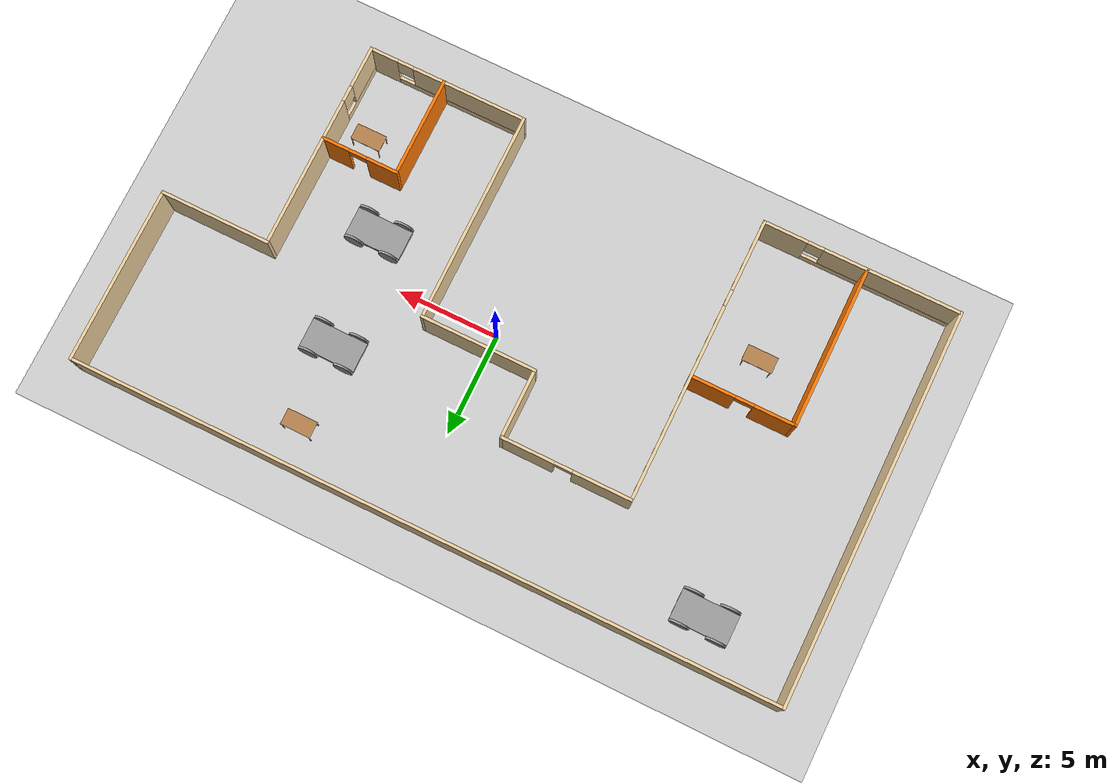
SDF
<sdf version="1.6">
 <world name="default">
  <model name="ground_plane">
   <static>1</static>
   <link name="link">
    <collision name="collision">
     <geometry><plane><normal>0 0 1</normal><size>100 100</size></plane></geometry>
     <surface><friction><ode><mu>100</mu><mu2>50</mu2></ode></friction></surface>
    </collision>
    <visual name="visual">
     <cast_shadows>0</cast_shadows>
     <geometry><plane><normal>0 0 1</normal><size>100 100</size></plane></geometry>
     <material>
      <script><uri>file://media/materials/scripts/gazebo.material</uri><name>Gazebo/Grey</name></script>
     </material>
    </visual>
   </link>
  </model>
  <light name="sun" type="directional">
   <pose>0 0 10 0 -0 0</pose>
   <diffuse>0.8 0.8 0.8 1</diffuse>
   <specular>0.2 0.2 0.2 1</specular>
   <attenuation>
    <range>1000</range>
    <constant>0.9</constant>
    <linear>0.01</linear>
    <quadratic>0.001</quadratic>
   </attenuation>
   <direction>-0.5 0.1 -0.9</direction>
  </light>
  <gravity>0 0 -9.8</gravity>
  <magnetic_field>6e-06 2.3e-05 -4.2e-05</magnetic_field>
  <atmosphere type="adiabatic"/>
  <physics name="default_physics" default="0" type="ode">
   <max_step_size>0.001</max_step_size>
   <real_time_factor>1</real_time_factor>
   <real_time_update_rate>1000</real_time_update_rate>
  </physics>
  <scene><ambient>0.4 0.4 0.4 1</ambient><background>0.7 0.7 0.7 1</background><shadows>1</shadows></scene>
  <spherical_coordinates>
   <surface_model>EARTH_WGS84</surface_model>
   <latitude_deg>0</latitude_deg>
   <longitude_deg>0</longitude_deg>
   <elevation>0</elevation>
   <heading_deg>0</heading_deg>
  </spherical_coordinates>
  <model name="appartment">
   <pose>-1.06068 0.00541 0 0 -0 0</pose>
   <link name="Wall_0">
    <collision name="Wall_0_Collision">
     <geometry><box><size>19.4596 0.15 2.5</size></box></geometry>
     <pose>0 0 1.25 0 -0 0</pose>
    </collision>
    <visual name="Wall_0_Visual">
     <pose>0 0 1.25 0 -0 0</pose>
     <geometry><box><size>19.4596 0.15 2.5</size></box></geometry>
     <material>
      <script><uri>file://media/materials/scripts/gazebo.material</uri><name>Gazebo/Grey</name></script>
      <ambient>0.921569 0.807843 0.615686 1</ambient>
     </material>
     <meta><layer>0</layer></meta>
    </visual>
    <pose>-17.4083 -0.020065 0 0 -0 1.5708</pose>
   </link>
   <link name="Wall_1">
    <collision name="Wall_1_Collision">
     <geometry><box><size>34.9669 0.15 2.5</size></box></geometry>
     <pose>0 0 1.25 0 -0 0</pose>
    </collision>
    <visual name="Wall_1_Visual">
     <pose>0 0 1.25 0 -0 0</pose>
     <geometry><box><size>34.9669 0.15 2.5</size></box></geometry>
     <material>
      <script><uri>file://media/materials/scripts/gazebo.material</uri><name>Gazebo/Grey</name></script>
      <ambient>0.921569 0.807843 0.615686 1</ambient>
     </material>
     <meta><layer>0</layer></meta>
    </visual>
    <pose>0 9.65496 0 0 -0 0.00115</pose>
   </link>
   <link name="Wall_10">
    <pose>-7.7415 -2.62504 0 0 0 -1.57076</pose>
    <visual name="Wall_10_Visual_0">
     <pose>-2.2093 0 1.25 0 -0 0</pose>
     <geometry><box><size>9.8314 0.15 2.5</size></box></geometry>
     <material>
      <script><uri>file://media/materials/scripts/gazebo.material</uri><name>Gazebo/Grey</name></script>
      <ambient>0.921569 0.807843 0.615686 1</ambient>
     </material>
     <meta><layer>0</layer></meta>
    </visual>
    <collision name="Wall_10_Collision_0">
     <geometry><box><size>9.8314 0.15 2.5</size></box></geometry>
     <pose>-2.2093 0 1.25 0 -0 0</pose>
    </collision>
    <visual name="Wall_10_Visual_1">
     <pose>4.9157 0 0.25 0 -0 0</pose>
     <geometry><box><size>4.4186 0.15 0.5</size></box></geometry>
     <material>
      <script><uri>file://media/materials/scripts/gazebo.material</uri><name>Gazebo/Grey</name></script>
      <ambient>0.921569 0.807843 0.615686 1</ambient>
     </material>
     <meta><layer>0</layer></meta>
    </visual>
    <collision name="Wall_10_Collision_1">
     <geometry><box><size>4.4186 0.15 0.5</size></box></geometry>
     <pose>4.9157 0 0.25 0 -0 0</pose>
    </collision>
    <visual name="Wall_10_Visual_2">
     <pose>5.3157 0 1.5 0 -0 0</pose>
     <geometry><box><size>3.6186 0.15 2</size></box></geometry>
     <material>
      <script><uri>file://media/materials/scripts/gazebo.material</uri><name>Gazebo/Grey</name></script>
      <ambient>0.921569 0.807843 0.615686 1</ambient>
     </material>
     <meta><layer>0</layer></meta>
    </visual>
    <collision name="Wall_10_Collision_2">
     <geometry><box><size>3.6186 0.15 2</size></box></geometry>
     <pose>5.3157 0 1.5 0 -0 0</pose>
    </collision>
    <visual name="Wall_10_Visual_3">
     <pose>3.1064 0 1.9 0 -0 0</pose>
     <geometry><box><size>0.8 0.15 1.2</size></box></geometry>
     <material>
      <script><uri>file://media/materials/scripts/gazebo.material</uri><name>Gazebo/Grey</name></script>
      <ambient>0.921569 0.807843 0.615686 1</ambient>
     </material>
     <meta><layer>0</layer></meta>
    </visual>
    <collision name="Wall_10_Collision_3">
     <geometry><box><size>0.8 0.15 1.2</size></box></geometry>
     <pose>3.1064 0 1.9 0 -0 0</pose>
    </collision>
   </link>
   <link name="Wall_11">
    <pose>-12.5748 -9.67507 0 0 -0 3.14159</pose>
    <visual name="Wall_11_Visual_0">
     <pose>-3.79039 0 1.25 0 -0 0</pose>
     <geometry><box><size>2.23622 0.15 2.5</size></box></geometry>
     <material>
      <script><uri>file://media/materials/scripts/gazebo.material</uri><name>Gazebo/Grey</name></script>
      <ambient>0.921569 0.807843 0.615686 1</ambient>
     </material>
     <meta><layer>0</layer></meta>
    </visual>
    <collision name="Wall_11_Collision_0">
     <geometry><box><size>2.23622 0.15 2.5</size></box></geometry>
     <pose>-3.79039 0 1.25 0 -0 0</pose>
    </collision>
    <visual name="Wall_11_Visual_1">
     <pose>1.11811 0 0.25 0 -0 0</pose>
     <geometry><box><size>7.58078 0.15 0.5</size></box></geometry>
     <material>
      <script><uri>file://media/materials/scripts/gazebo.material</uri><name>Gazebo/Grey</name></script>
      <ambient>0.921569 0.807843 0.615686 1</ambient>
     </material>
     <meta><layer>0</layer></meta>
    </visual>
    <collision name="Wall_11_Collision_1">
     <geometry><box><size>7.58078 0.15 0.5</size></box></geometry>
     <pose>1.11811 0 0.25 0 -0 0</pose>
    </collision>
    <visual name="Wall_11_Visual_2">
     <pose>1.51811 0 1.5 0 -0 0</pose>
     <geometry><box><size>6.78078 0.15 2</size></box></geometry>
     <material>
      <script><uri>file://media/materials/scripts/gazebo.material</uri><name>Gazebo/Grey</name></script>
      <ambient>0.921569 0.807843 0.615686 1</ambient>
     </material>
     <meta><layer>0</layer></meta>
    </visual>
    <collision name="Wall_11_Collision_2">
     <geometry><box><size>6.78078 0.15 2</size></box></geometry>
     <pose>1.51811 0 1.5 0 -0 0</pose>
    </collision>
    <visual name="Wall_11_Visual_3">
     <pose>-2.27228 0 1.9 0 -0 0</pose>
     <geometry><box><size>0.8 0.15 1.2</size></box></geometry>
     <material>
      <script><uri>file://media/materials/scripts/gazebo.material</uri><name>Gazebo/Grey</name></script>
      <ambient>0.921569 0.807843 0.615686 1</ambient>
     </material>
     <meta><layer>0</layer></meta>
    </visual>
    <collision name="Wall_11_Collision_3">
     <geometry><box><size>0.8 0.15 1.2</size></box></geometry>
     <pose>-2.27228 0 1.9 0 -0 0</pose>
    </collision>
   </link>
   <link name="Wall_13">
    <collision name="Wall_13_Collision">
     <geometry><box><size>5 0.15 2.5</size></box></geometry>
     <pose>0 0 1.25 0 -0 0</pose>
    </collision>
    <visual name="Wall_13_Visual">
     <pose>0 0 1.25 0 -0 0</pose>
     <geometry><box><size>5 0.15 2.5</size></box></geometry>
     <material>
      <script><uri>file://media/materials/scripts/gazebo.material</uri><name>Gazebo/Grey</name></script>
      <ambient>0.996078 0.47451 0.0196078 1</ambient>
     </material>
     <meta><layer>0</layer></meta>
    </visual>
    <pose>8.30689 -6.85928 0 0 -0 1.57087</pose>
   </link>
   <link name="Wall_14">
    <pose>10.1827 -4.43407 0 0 -0 0</pose>
    <visual name="Wall_14_Visual_0">
     <pose>-1.15332 0 1.25 0 -0 0</pose>
     <geometry><box><size>1.59536 0.15 2.5</size></box></geometry>
     <material>
      <script><uri>file://media/materials/scripts/gazebo.material</uri><name>Gazebo/Grey</name></script>
      <ambient>0.996078 0.47451 0.0196078 1</ambient>
     </material>
     <meta><layer>0</layer></meta>
    </visual>
    <collision name="Wall_14_Collision_0">
     <geometry><box><size>1.59536 0.15 2.5</size></box></geometry>
     <pose>-1.15332 0 1.25 0 -0 0</pose>
    </collision>
    <visual name="Wall_14_Visual_1">
     <pose>1.24768 0 1.25 0 -0 0</pose>
     <geometry><box><size>1.40664 0.15 2.5</size></box></geometry>
     <material>
      <script><uri>file://media/materials/scripts/gazebo.material</uri><name>Gazebo/Grey</name></script>
      <ambient>0.996078 0.47451 0.0196078 1</ambient>
     </material>
     <meta><layer>0</layer></meta>
    </visual>
    <collision name="Wall_14_Collision_1">
     <geometry><box><size>1.40664 0.15 2.5</size></box></geometry>
     <pose>1.24768 0 1.25 0 -0 0</pose>
    </collision>
    <visual name="Wall_14_Visual_2">
     <pose>0.094359 0 2.25 0 -0 0</pose>
     <geometry><box><size>0.9 0.15 0.5</size></box></geometry>
     <material>
      <script><uri>file://media/materials/scripts/gazebo.material</uri><name>Gazebo/Grey</name></script>
      <ambient>0.996078 0.47451 0.0196078 1</ambient>
     </material>
     <meta><layer>0</layer></meta>
    </visual>
    <collision name="Wall_14_Collision_2">
     <geometry><box><size>0.9 0.15 0.5</size></box></geometry>
     <pose>0.094359 0 2.25 0 -0 0</pose>
    </collision>
   </link>
   <link name="Wall_16">
    <pose>-10.2844 -1.75625 0 0 -0 3.14159</pose>
    <visual name="Wall_16_Visual_0">
     <pose>-1.4933 0 1.25 0 -0 0</pose>
     <geometry><box><size>2.26341 0.15 2.5</size></box></geometry>
     <material>
      <script><uri>file://media/materials/scripts/gazebo.material</uri><name>Gazebo/Grey</name></script>
      <ambient>0.996078 0.47451 0.0196078 1</ambient>
     </material>
     <meta><layer>0</layer></meta>
    </visual>
    <collision name="Wall_16_Collision_0">
     <geometry><box><size>2.26341 0.15 2.5</size></box></geometry>
     <pose>-1.4933 0 1.25 0 -0 0</pose>
    </collision>
    <visual name="Wall_16_Visual_1">
     <pose>1.5817 0 1.25 0 -0 0</pose>
     <geometry><box><size>2.08659 0.15 2.5</size></box></geometry>
     <material>
      <script><uri>file://media/materials/scripts/gazebo.material</uri><name>Gazebo/Grey</name></script>
      <ambient>0.996078 0.47451 0.0196078 1</ambient>
     </material>
     <meta><layer>0</layer></meta>
    </visual>
    <collision name="Wall_16_Collision_1">
     <geometry><box><size>2.08659 0.15 2.5</size></box></geometry>
     <pose>1.5817 0 1.25 0 -0 0</pose>
    </collision>
    <visual name="Wall_16_Visual_2">
     <pose>0.088408 0 2.25 0 -0 0</pose>
     <geometry><box><size>0.9 0.15 0.5</size></box></geometry>
     <material>
      <script><uri>file://media/materials/scripts/gazebo.material</uri><name>Gazebo/Grey</name></script>
      <ambient>0.996078 0.47451 0.0196078 1</ambient>
     </material>
     <meta><layer>0</layer></meta>
    </visual>
    <collision name="Wall_16_Collision_2">
     <geometry><box><size>0.9 0.15 0.5</size></box></geometry>
     <pose>0.088408 0 2.25 0 -0 0</pose>
    </collision>
   </link>
   <link name="Wall_17">
    <collision name="Wall_17_Collision">
     <geometry><box><size>8 0.15 2.5</size></box></geometry>
     <pose>0 0 1.25 0 -0 0</pose>
    </collision>
    <visual name="Wall_17_Visual">
     <pose>0 0 1.25 0 -0 0</pose>
     <geometry><box><size>8 0.15 2.5</size></box></geometry>
     <material>
      <script><uri>file://media/materials/scripts/gazebo.material</uri><name>Gazebo/Grey</name></script>
      <ambient>0.996078 0.47451 0.0196078 1</ambient>
     </material>
     <meta><layer>0</layer></meta>
    </visual>
    <pose>-12.8344 -5.68124 0 0 0 -1.5708</pose>
   </link>
   <link name="Wall_2">
    <collision name="Wall_2_Collision">
     <geometry><box><size>8.75 0.15 2.5</size></box></geometry>
     <pose>0 0 1.25 0 -0 0</pose>
    </collision>
    <visual name="Wall_2_Visual">
     <pose>0 0 1.25 0 -0 0</pose>
     <geometry><box><size>8.75 0.15 2.5</size></box></geometry>
     <material>
      <script><uri>file://media/materials/scripts/gazebo.material</uri><name>Gazebo/Grey</name></script>
      <ambient>0.921569 0.807843 0.615686 1</ambient>
     </material>
     <meta><layer>0</layer></meta>
    </visual>
    <pose>17.4083 5.37498 0 0 0 -1.5708</pose>
   </link>
   <link name="Wall_3">
    <collision name="Wall_3_Collision">
     <geometry><box><size>5.5 0.15 2.5</size></box></geometry>
     <pose>0 0 1.25 0 -0 0</pose>
    </collision>
    <visual name="Wall_3_Visual">
     <pose>0 0 1.25 0 -0 0</pose>
     <geometry><box><size>5.5 0.15 2.5</size></box></geometry>
     <material>
      <script><uri>file://media/materials/scripts/gazebo.material</uri><name>Gazebo/Grey</name></script>
      <ambient>0.921569 0.807843 0.615686 1</ambient>
     </material>
     <meta><layer>0</layer></meta>
    </visual>
    <pose>14.7333 1.07498 0 0 -0 3.14159</pose>
   </link>
   <link name="Wall_4">
    <pose>12.0583 -4.10002 0 0 0 -1.5708</pose>
    <visual name="Wall_4_Visual_0">
     <pose>-1.46402 0 1.25 0 -0 0</pose>
     <geometry><box><size>7.57196 0.15 2.5</size></box></geometry>
     <material>
      <script><uri>file://media/materials/scripts/gazebo.material</uri><name>Gazebo/Grey</name></script>
      <ambient>0.921569 0.807843 0.615686 1</ambient>
     </material>
     <meta><layer>0</layer></meta>
    </visual>
    <collision name="Wall_4_Collision_0">
     <geometry><box><size>7.57196 0.15 2.5</size></box></geometry>
     <pose>-1.46402 0 1.25 0 -0 0</pose>
    </collision>
    <visual name="Wall_4_Visual_1">
     <pose>3.78598 0 0.25 0 -0 0</pose>
     <geometry><box><size>2.92803 0.15 0.5</size></box></geometry>
     <material>
      <script><uri>file://media/materials/scripts/gazebo.material</uri><name>Gazebo/Grey</name></script>
      <ambient>0.921569 0.807843 0.615686 1</ambient>
     </material>
     <meta><layer>0</layer></meta>
    </visual>
    <collision name="Wall_4_Collision_1">
     <geometry><box><size>2.92803 0.15 0.5</size></box></geometry>
     <pose>3.78598 0 0.25 0 -0 0</pose>
    </collision>
    <visual name="Wall_4_Visual_2">
     <pose>4.18598 0 1.5 0 -0 0</pose>
     <geometry><box><size>2.12804 0.15 2</size></box></geometry>
     <material>
      <script><uri>file://media/materials/scripts/gazebo.material</uri><name>Gazebo/Grey</name></script>
      <ambient>0.921569 0.807843 0.615686 1</ambient>
     </material>
     <meta><layer>0</layer></meta>
    </visual>
    <collision name="Wall_4_Collision_2">
     <geometry><box><size>2.12804 0.15 2</size></box></geometry>
     <pose>4.18598 0 1.5 0 -0 0</pose>
    </collision>
    <visual name="Wall_4_Visual_3">
     <pose>2.72196 0 1.9 0 -0 0</pose>
     <geometry><box><size>0.8 0.15 1.2</size></box></geometry>
     <material>
      <script><uri>file://media/materials/scripts/gazebo.material</uri><name>Gazebo/Grey</name></script>
      <ambient>0.921569 0.807843 0.615686 1</ambient>
     </material>
     <meta><layer>0</layer></meta>
    </visual>
    <collision name="Wall_4_Collision_3">
     <geometry><box><size>0.8 0.15 1.2</size></box></geometry>
     <pose>2.72196 0 1.9 0 -0 0</pose>
    </collision>
   </link>
   <link name="Wall_5">
    <pose>8.13328 -9.27502 0 0 -0 3.14159</pose>
    <visual name="Wall_5_Visual_0">
     <pose>-3.2719 0 1.25 0 -0 0</pose>
     <geometry><box><size>1.4562 0.15 2.5</size></box></geometry>
     <material>
      <script><uri>file://media/materials/scripts/gazebo.material</uri><name>Gazebo/Grey</name></script>
      <ambient>0.921569 0.807843 0.615686 1</ambient>
     </material>
     <meta><layer>0</layer></meta>
    </visual>
    <collision name="Wall_5_Collision_0">
     <geometry><box><size>1.4562 0.15 2.5</size></box></geometry>
     <pose>-3.2719 0 1.25 0 -0 0</pose>
    </collision>
    <visual name="Wall_5_Visual_1">
     <pose>0.728102 0 0.25 0 -0 0</pose>
     <geometry><box><size>6.5438 0.15 0.5</size></box></geometry>
     <material>
      <script><uri>file://media/materials/scripts/gazebo.material</uri><name>Gazebo/Grey</name></script>
      <ambient>0.921569 0.807843 0.615686 1</ambient>
     </material>
     <meta><layer>0</layer></meta>
    </visual>
    <collision name="Wall_5_Collision_1">
     <geometry><box><size>6.5438 0.15 0.5</size></box></geometry>
     <pose>0.728102 0 0.25 0 -0 0</pose>
    </collision>
    <visual name="Wall_5_Visual_2">
     <pose>1.1281 0 1.5 0 -0 0</pose>
     <geometry><box><size>5.7438 0.15 2</size></box></geometry>
     <material>
      <script><uri>file://media/materials/scripts/gazebo.material</uri><name>Gazebo/Grey</name></script>
      <ambient>0.921569 0.807843 0.615686 1</ambient>
     </material>
     <meta><layer>0</layer></meta>
    </visual>
    <collision name="Wall_5_Collision_2">
     <geometry><box><size>5.7438 0.15 2</size></box></geometry>
     <pose>1.1281 0 1.5 0 -0 0</pose>
    </collision>
    <visual name="Wall_5_Visual_3">
     <pose>-2.14379 0 1.9 0 -0 0</pose>
     <geometry><box><size>0.8 0.15 1.2</size></box></geometry>
     <material>
      <script><uri>file://media/materials/scripts/gazebo.material</uri><name>Gazebo/Grey</name></script>
      <ambient>0.921569 0.807843 0.615686 1</ambient>
     </material>
     <meta><layer>0</layer></meta>
    </visual>
    <collision name="Wall_5_Collision_3">
     <geometry><box><size>0.8 0.15 1.2</size></box></geometry>
     <pose>-2.14379 0 1.9 0 -0 0</pose>
    </collision>
   </link>
   <link name="Wall_6">
    <collision name="Wall_6_Collision">
     <geometry><box><size>10.5 0.15 2.5</size></box></geometry>
     <pose>0 0 1.25 0 -0 0</pose>
    </collision>
    <visual name="Wall_6_Visual">
     <pose>0 0 1.25 0 -0 0</pose>
     <geometry><box><size>10.5 0.15 2.5</size></box></geometry>
     <material>
      <script><uri>file://media/materials/scripts/gazebo.material</uri><name>Gazebo/Grey</name></script>
      <ambient>0.921569 0.807843 0.615686 1</ambient>
     </material>
     <meta><layer>0</layer></meta>
    </visual>
    <pose>4.20828 -4.10002 0 0 -0 1.5708</pose>
   </link>
   <link name="Wall_7">
    <collision name="Wall_7_Collision">
     <geometry><box><size>5.75 0.15 2.5</size></box></geometry>
     <pose>0 0 1.25 0 -0 0</pose>
    </collision>
    <visual name="Wall_7_Visual">
     <pose>0 0 1.25 0 -0 0</pose>
     <geometry><box><size>5.75 0.15 2.5</size></box></geometry>
     <material>
      <script><uri>file://media/materials/scripts/gazebo.material</uri><name>Gazebo/Grey</name></script>
      <ambient>0.921569 0.807843 0.615686 1</ambient>
     </material>
     <meta><layer>0</layer></meta>
    </visual>
    <pose>1.40828 1.07498 0 0 -0 3.14159</pose>
   </link>
   <link name="Wall_8">
    <collision name="Wall_8_Collision">
     <geometry><box><size>3.5 0.15 2.5</size></box></geometry>
     <pose>0 0 1.25 0 -0 0</pose>
    </collision>
    <visual name="Wall_8_Visual">
     <pose>0 0 1.25 0 -0 0</pose>
     <geometry><box><size>3.5 0.15 2.5</size></box></geometry>
     <material>
      <script><uri>file://media/materials/scripts/gazebo.material</uri><name>Gazebo/Grey</name></script>
      <ambient>0.921569 0.807843 0.615686 1</ambient>
     </material>
     <meta><layer>0</layer></meta>
    </visual>
    <pose>-1.39172 2.74998 0 0 -0 1.5708</pose>
   </link>
   <link name="Wall_9">
    <pose>-4.56672 4.42498 0 0 -0 3.14159</pose>
    <visual name="Wall_9_Visual_0">
     <pose>-1.91954 0 1.25 0 -0 0</pose>
     <geometry><box><size>2.66093 0.15 2.5</size></box></geometry>
     <material>
      <script><uri>file://media/materials/scripts/gazebo.material</uri><name>Gazebo/Grey</name></script>
      <ambient>0.921569 0.807843 0.615686 1</ambient>
     </material>
     <meta><layer>0</layer></meta>
    </visual>
    <collision name="Wall_9_Collision_0">
     <geometry><box><size>2.66093 0.15 2.5</size></box></geometry>
     <pose>-1.91954 0 1.25 0 -0 0</pose>
    </collision>
    <visual name="Wall_9_Visual_1">
     <pose>1.78046 0 1.25 0 -0 0</pose>
     <geometry><box><size>2.93907 0.15 2.5</size></box></geometry>
     <material>
      <script><uri>file://media/materials/scripts/gazebo.material</uri><name>Gazebo/Grey</name></script>
      <ambient>0.921569 0.807843 0.615686 1</ambient>
     </material>
     <meta><layer>0</layer></meta>
    </visual>
    <collision name="Wall_9_Collision_1">
     <geometry><box><size>2.93907 0.15 2.5</size></box></geometry>
     <pose>1.78046 0 1.25 0 -0 0</pose>
    </collision>
    <visual name="Wall_9_Visual_2">
     <pose>-0.139072 0 2.25 0 -0 0</pose>
     <geometry><box><size>0.9 0.15 0.5</size></box></geometry>
     <material>
      <script><uri>file://media/materials/scripts/gazebo.material</uri><name>Gazebo/Grey</name></script>
      <ambient>0.921569 0.807843 0.615686 1</ambient>
     </material>
     <meta><layer>0</layer></meta>
    </visual>
    <collision name="Wall_9_Collision_2">
     <geometry><box><size>0.9 0.15 0.5</size></box></geometry>
     <pose>-0.139072 0 2.25 0 -0 0</pose>
    </collision>
   </link>
   <static>1</static>
  </model>
  <model name="robot">
   <link name="link_0">
    <pose>-1e-06 -2e-06 -0.017894 0 -0 0</pose>
    <inertial>
     <mass>0.791661</mass>
     <inertia>
      <ixx>0.14552</ixx>
      <ixy>0</ixy>
      <ixz>0</ixz>
      <iyy>0.516326</iyy>
      <iyz>0</iyz>
      <izz>0.656947</izz>
     </inertia>
    </inertial>
    <visual name="visual">
     <geometry><box><size>2.79094 1.47264 0.192699</size></box></geometry>
     <material>
      <lighting>1</lighting>
      <script><uri>file://media/materials/scripts/gazebo.material</uri><name>Gazebo/Grey</name></script>
      <shader type="pixel"/>
      <ambient>0.3 0.3 0.3 1</ambient>
      <diffuse>0.7 0.7 0.7 1</diffuse>
      <specular>0.01 0.01 0.01 1</specular>
      <emissive>0 0 0 1</emissive>
     </material>
    </visual>
    <collision name="collision">
     <geometry><box><size>2.79094 1.47264 0.192699</size></box></geometry>
     <surface>
      <friction>
       <ode><mu>1</mu><mu2>1</mu2><fdir1>0 0 0</fdir1><slip1>0</slip1><slip2>0</slip2></ode>
       <torsional>
        <coefficient>1</coefficient>
        <patch_radius>0</patch_radius>
        <surface_radius>0</surface_radius>
        <use_patch_radius>1</use_patch_radius>
        <ode><slip>0</slip></ode>
       </torsional>
      </friction>
      <bounce><restitution_coefficient>0</restitution_coefficient><threshold>1e+06</threshold></bounce>
      <contact>
       <collide_without_contact>0</collide_without_contact>
       <collide_without_contact_bitmask>1</collide_without_contact_bitmask>
       <collide_bitmask>1</collide_bitmask>
       <ode>
        <soft_cfm>0</soft_cfm>
        <soft_erp>0.2</soft_erp>
        <kp>1e+13</kp>
        <kd>1</kd>
        <max_vel>0.01</max_vel>
        <min_depth>0</min_depth>
       </ode>
       <bullet>
        <split_impulse>1</split_impulse>
        <split_impulse_penetration_threshold>-0.01</split_impulse_penetration_threshold>
        <soft_cfm>0</soft_cfm>
        <soft_erp>0.2</soft_erp>
        <kp>1e+13</kp>
        <kd>1</kd>
       </bullet>
      </contact>
     </surface>
    </collision>
   </link>
   <link name="link_1">
    <pose>0.895468 -0.796371 0.004474 1.58338 -0 0</pose>
    <inertial>
     <mass>0.107521</mass>
     <inertia>
      <ixx>0.00682364</ixx>
      <ixy>0</ixy>
      <ixz>0</ixz>
      <iyy>0.00682364</iyy>
      <iyz>0</iyz>
      <izz>0.0134401</izz>
     </inertia>
    </inertial>
    <visual name="visual">
     <geometry><cylinder><radius>0.5</radius><length>0.107521</length></cylinder></geometry>
     <material>
      <lighting>1</lighting>
      <script><uri>file://media/materials/scripts/gazebo.material</uri><name>Gazebo/Grey</name></script>
      <shader type="pixel"><normal_map>__default__</normal_map></shader>
      <ambient>0.3 0.3 0.3 1</ambient>
      <diffuse>0.7 0.7 0.7 1</diffuse>
      <specular>0.01 0.01 0.01 1</specular>
      <emissive>0 0 0 1</emissive>
     </material>
    </visual>
    <collision name="collision">
     <geometry><cylinder><radius>0.5</radius><length>0.107521</length></cylinder></geometry>
     <surface>
      <friction>
       <ode><mu>1</mu><mu2>1</mu2><fdir1>0 0 0</fdir1><slip1>0</slip1><slip2>0</slip2></ode>
       <torsional>
        <coefficient>1</coefficient>
        <patch_radius>0</patch_radius>
        <surface_radius>0</surface_radius>
        <use_patch_radius>1</use_patch_radius>
        <ode><slip>0</slip></ode>
       </torsional>
      </friction>
      <bounce><restitution_coefficient>0</restitution_coefficient><threshold>1e+06</threshold></bounce>
      <contact>
       <collide_without_contact>0</collide_without_contact>
       <collide_without_contact_bitmask>1</collide_without_contact_bitmask>
       <collide_bitmask>1</collide_bitmask>
       <ode>
        <soft_cfm>0</soft_cfm>
        <soft_erp>0.2</soft_erp>
        <kp>1e+13</kp>
        <kd>1</kd>
        <max_vel>0.01</max_vel>
        <min_depth>0</min_depth>
       </ode>
       <bullet>
        <split_impulse>1</split_impulse>
        <split_impulse_penetration_threshold>-0.01</split_impulse_penetration_threshold>
        <soft_cfm>0</soft_cfm>
        <soft_erp>0.2</soft_erp>
        <kp>1e+13</kp>
        <kd>1</kd>
       </bullet>
      </contact>
     </surface>
    </collision>
   </link>
   <link name="link_1_clone">
    <pose>0.895468 0.796367 0.004474 1.58338 -0 0</pose>
    <inertial>
     <mass>0.107521</mass>
     <inertia>
      <ixx>0.00682364</ixx>
      <ixy>0</ixy>
      <ixz>0</ixz>
      <iyy>0.00682364</iyy>
      <iyz>0</iyz>
      <izz>0.0134401</izz>
     </inertia>
    </inertial>
    <visual name="visual">
     <geometry><cylinder><radius>0.5</radius><length>0.107521</length></cylinder></geometry>
     <material>
      <lighting>1</lighting>
      <script><uri>file://media/materials/scripts/gazebo.material</uri><name>Gazebo/Grey</name></script>
      <shader type="pixel"><normal_map>__default__</normal_map></shader>
      <ambient>0.3 0.3 0.3 1</ambient>
      <diffuse>0.7 0.7 0.7 1</diffuse>
      <specular>0.01 0.01 0.01 1</specular>
      <emissive>0 0 0 1</emissive>
     </material>
    </visual>
    <collision name="collision">
     <geometry><cylinder><radius>0.5</radius><length>0.107521</length></cylinder></geometry>
     <surface>
      <friction>
       <ode><mu>1</mu><mu2>1</mu2><fdir1>0 0 0</fdir1><slip1>0</slip1><slip2>0</slip2></ode>
       <torsional>
        <coefficient>1</coefficient>
        <patch_radius>0</patch_radius>
        <surface_radius>0</surface_radius>
        <use_patch_radius>1</use_patch_radius>
        <ode><slip>0</slip></ode>
       </torsional>
      </friction>
      <bounce><restitution_coefficient>0</restitution_coefficient><threshold>1e+06</threshold></bounce>
      <contact>
       <collide_without_contact>0</collide_without_contact>
       <collide_without_contact_bitmask>1</collide_without_contact_bitmask>
       <collide_bitmask>1</collide_bitmask>
       <ode>
        <soft_cfm>0</soft_cfm>
        <soft_erp>0.2</soft_erp>
        <kp>1e+13</kp>
        <kd>1</kd>
        <max_vel>0.01</max_vel>
        <min_depth>0</min_depth>
       </ode>
       <bullet>
        <split_impulse>1</split_impulse>
        <split_impulse_penetration_threshold>-0.01</split_impulse_penetration_threshold>
        <soft_cfm>0</soft_cfm>
        <soft_erp>0.2</soft_erp>
        <kp>1e+13</kp>
        <kd>1</kd>
       </bullet>
      </contact>
     </surface>
    </collision>
   </link>
   <link name="link_1_clone_clone">
    <pose>-0.895471 -0.796371 0.004474 1.58338 -0 0</pose>
    <inertial>
     <mass>0.107521</mass>
     <inertia>
      <ixx>0.00682364</ixx>
      <ixy>0</ixy>
      <ixz>0</ixz>
      <iyy>0.00682364</iyy>
      <iyz>0</iyz>
      <izz>0.0134401</izz>
     </inertia>
    </inertial>
    <visual name="visual">
     <geometry><cylinder><radius>0.5</radius><length>0.107521</length></cylinder></geometry>
     <material>
      <lighting>1</lighting>
      <script><uri>file://media/materials/scripts/gazebo.material</uri><name>Gazebo/Grey</name></script>
      <shader type="pixel"><normal_map>__default__</normal_map></shader>
      <ambient>0.3 0.3 0.3 1</ambient>
      <diffuse>0.7 0.7 0.7 1</diffuse>
      <specular>0.01 0.01 0.01 1</specular>
      <emissive>0 0 0 1</emissive>
     </material>
    </visual>
    <collision name="collision">
     <geometry><cylinder><radius>0.5</radius><length>0.107521</length></cylinder></geometry>
     <surface>
      <friction>
       <ode><mu>1</mu><mu2>1</mu2><fdir1>0 0 0</fdir1><slip1>0</slip1><slip2>0</slip2></ode>
       <torsional>
        <coefficient>1</coefficient>
        <patch_radius>0</patch_radius>
        <surface_radius>0</surface_radius>
        <use_patch_radius>1</use_patch_radius>
        <ode><slip>0</slip></ode>
       </torsional>
      </friction>
      <bounce><restitution_coefficient>0</restitution_coefficient><threshold>1e+06</threshold></bounce>
      <contact>
       <collide_without_contact>0</collide_without_contact>
       <collide_without_contact_bitmask>1</collide_without_contact_bitmask>
       <collide_bitmask>1</collide_bitmask>
       <ode>
        <soft_cfm>0</soft_cfm>
        <soft_erp>0.2</soft_erp>
        <kp>1e+13</kp>
        <kd>1</kd>
        <max_vel>0.01</max_vel>
        <min_depth>0</min_depth>
       </ode>
       <bullet>
        <split_impulse>1</split_impulse>
        <split_impulse_penetration_threshold>-0.01</split_impulse_penetration_threshold>
        <soft_cfm>0</soft_cfm>
        <soft_erp>0.2</soft_erp>
        <kp>1e+13</kp>
        <kd>1</kd>
       </bullet>
      </contact>
     </surface>
    </collision>
   </link>
   <link name="link_1_clone_clone_clone">
    <pose>-0.895471 0.796367 0.004474 1.58338 -0 0</pose>
    <inertial>
     <mass>0.107521</mass>
     <inertia>
      <ixx>0.00682364</ixx>
      <ixy>0</ixy>
      <ixz>0</ixz>
      <iyy>0.00682364</iyy>
      <iyz>0</iyz>
      <izz>0.0134401</izz>
     </inertia>
    </inertial>
    <visual name="visual">
     <geometry><cylinder><radius>0.5</radius><length>0.107521</length></cylinder></geometry>
     <material>
      <lighting>1</lighting>
      <script><uri>file://media/materials/scripts/gazebo.material</uri><name>Gazebo/Grey</name></script>
      <shader type="pixel"><normal_map>__default__</normal_map></shader>
      <ambient>0.3 0.3 0.3 1</ambient>
      <diffuse>0.7 0.7 0.7 1</diffuse>
      <specular>0.01 0.01 0.01 1</specular>
      <emissive>0 0 0 1</emissive>
     </material>
    </visual>
    <collision name="collision">
     <geometry><cylinder><radius>0.5</radius><length>0.107521</length></cylinder></geometry>
     <surface>
      <friction>
       <ode><mu>1</mu><mu2>1</mu2><fdir1>0 0 0</fdir1><slip1>0</slip1><slip2>0</slip2></ode>
       <torsional>
        <coefficient>1</coefficient>
        <patch_radius>0</patch_radius>
        <surface_radius>0</surface_radius>
        <use_patch_radius>1</use_patch_radius>
        <ode><slip>0</slip></ode>
       </torsional>
      </friction>
      <bounce><restitution_coefficient>0</restitution_coefficient><threshold>1e+06</threshold></bounce>
      <contact>
       <collide_without_contact>0</collide_without_contact>
       <collide_without_contact_bitmask>1</collide_without_contact_bitmask>
       <collide_bitmask>1</collide_bitmask>
       <ode>
        <soft_cfm>0</soft_cfm>
        <soft_erp>0.2</soft_erp>
        <kp>1e+13</kp>
        <kd>1</kd>
        <max_vel>0.01</max_vel>
        <min_depth>0</min_depth>
       </ode>
       <bullet>
        <split_impulse>1</split_impulse>
        <split_impulse_penetration_threshold>-0.01</split_impulse_penetration_threshold>
        <soft_cfm>0</soft_cfm>
        <soft_erp>0.2</soft_erp>
        <kp>1e+13</kp>
        <kd>1</kd>
       </bullet>
      </contact>
     </surface>
    </collision>
   </link>
   <joint name="link_0_JOINT_0" type="revolute">
    <parent>link_0</parent>
    <child>link_1</child>
    <axis>
     <xyz>1 0 0</xyz>
     <use_parent_model_frame>0</use_parent_model_frame>
     <limit>
      <lower>-1.79769e+308</lower>
      <upper>1.79769e+308</upper>
      <effort>-1</effort>
      <velocity>-1</velocity>
     </limit>
     <dynamics>
      <spring_reference>0</spring_reference>
      <spring_stiffness>0</spring_stiffness>
      <damping>0</damping>
     </dynamics>
    </axis>
    <physics>
     <ode><limit><cfm>0</cfm><erp>0.2</erp></limit><suspension><cfm>0</cfm><erp>0.2</erp></suspension></ode>
    </physics>
   </joint>
   <joint name="link_0_JOINT_1" type="revolute">
    <parent>link_0</parent>
    <child>link_1_clone</child>
    <axis>
     <xyz>1 0 0</xyz>
     <use_parent_model_frame>0</use_parent_model_frame>
     <limit>
      <lower>-1.79769e+308</lower>
      <upper>1.79769e+308</upper>
      <effort>-1</effort>
      <velocity>-1</velocity>
     </limit>
     <dynamics>
      <spring_reference>0</spring_reference>
      <spring_stiffness>0</spring_stiffness>
      <damping>0</damping>
     </dynamics>
    </axis>
    <physics>
     <ode><limit><cfm>0</cfm><erp>0.2</erp></limit><suspension><cfm>0</cfm><erp>0.2</erp></suspension></ode>
    </physics>
   </joint>
   <joint name="link_0_JOINT_2" type="revolute">
    <parent>link_0</parent>
    <child>link_1_clone_clone</child>
    <axis>
     <xyz>1 0 0</xyz>
     <use_parent_model_frame>0</use_parent_model_frame>
     <limit>
      <lower>-1.79769e+308</lower>
      <upper>1.79769e+308</upper>
      <effort>-1</effort>
      <velocity>-1</velocity>
     </limit>
     <dynamics>
      <spring_reference>0</spring_reference>
      <spring_stiffness>0</spring_stiffness>
      <damping>0</damping>
     </dynamics>
    </axis>
    <physics>
     <ode><limit><cfm>0</cfm><erp>0.2</erp></limit><suspension><cfm>0</cfm><erp>0.2</erp></suspension></ode>
    </physics>
   </joint>
   <joint name="link_0_JOINT_3" type="revolute">
    <parent>link_0</parent>
    <child>link_1_clone_clone_clone</child>
    <axis>
     <xyz>1 0 0</xyz>
     <use_parent_model_frame>0</use_parent_model_frame>
     <limit>
      <lower>-1.79769e+308</lower>
      <upper>1.79769e+308</upper>
      <effort>-1</effort>
      <velocity>-1</velocity>
     </limit>
     <dynamics>
      <spring_reference>0</spring_reference>
      <spring_stiffness>0</spring_stiffness>
      <damping>0</damping>
     </dynamics>
    </axis>
    <physics>
     <ode><limit><cfm>0</cfm><erp>0.2</erp></limit><suspension><cfm>0</cfm><erp>0.2</erp></suspension></ode>
    </physics>
   </joint>
   <static>0</static>
   <pose>6.49599 3.70017 0.495526 0 0 -0.000138</pose>
  </model>
  <model name="robot_0">
   <link name="link_0">
    <pose>-1e-06 -2e-06 -0.017894 0 -0 0</pose>
    <inertial>
     <mass>0.791661</mass>
     <inertia>
      <ixx>0.14552</ixx>
      <ixy>0</ixy>
      <ixz>0</ixz>
      <iyy>0.516326</iyy>
      <iyz>0</iyz>
      <izz>0.656947</izz>
     </inertia>
    </inertial>
    <visual name="visual">
     <geometry><box><size>2.79094 1.47264 0.192699</size></box></geometry>
     <material>
      <lighting>1</lighting>
      <script><uri>file://media/materials/scripts/gazebo.material</uri><name>Gazebo/Grey</name></script>
      <shader type="pixel"/>
      <ambient>0.3 0.3 0.3 1</ambient>
      <diffuse>0.7 0.7 0.7 1</diffuse>
      <specular>0.01 0.01 0.01 1</specular>
      <emissive>0 0 0 1</emissive>
     </material>
    </visual>
    <collision name="collision">
     <geometry><box><size>2.79094 1.47264 0.192699</size></box></geometry>
     <surface>
      <friction>
       <ode><mu>1</mu><mu2>1</mu2><fdir1>0 0 0</fdir1><slip1>0</slip1><slip2>0</slip2></ode>
       <torsional>
        <coefficient>1</coefficient>
        <patch_radius>0</patch_radius>
        <surface_radius>0</surface_radius>
        <use_patch_radius>1</use_patch_radius>
        <ode><slip>0</slip></ode>
       </torsional>
      </friction>
      <bounce><restitution_coefficient>0</restitution_coefficient><threshold>1e+06</threshold></bounce>
      <contact>
       <collide_without_contact>0</collide_without_contact>
       <collide_without_contact_bitmask>1</collide_without_contact_bitmask>
       <collide_bitmask>1</collide_bitmask>
       <ode>
        <soft_cfm>0</soft_cfm>
        <soft_erp>0.2</soft_erp>
        <kp>1e+13</kp>
        <kd>1</kd>
        <max_vel>0.01</max_vel>
        <min_depth>0</min_depth>
       </ode>
       <bullet>
        <split_impulse>1</split_impulse>
        <split_impulse_penetration_threshold>-0.01</split_impulse_penetration_threshold>
        <soft_cfm>0</soft_cfm>
        <soft_erp>0.2</soft_erp>
        <kp>1e+13</kp>
        <kd>1</kd>
       </bullet>
      </contact>
     </surface>
    </collision>
   </link>
   <link name="link_1">
    <pose>0.895468 -0.796371 0.004474 1.58338 -0 0</pose>
    <inertial>
     <mass>0.107521</mass>
     <inertia>
      <ixx>0.00682364</ixx>
      <ixy>0</ixy>
      <ixz>0</ixz>
      <iyy>0.00682364</iyy>
      <iyz>0</iyz>
      <izz>0.0134401</izz>
     </inertia>
    </inertial>
    <visual name="visual">
     <geometry><cylinder><radius>0.5</radius><length>0.107521</length></cylinder></geometry>
     <material>
      <lighting>1</lighting>
      <script><uri>file://media/materials/scripts/gazebo.material</uri><name>Gazebo/Grey</name></script>
      <shader type="pixel"><normal_map>__default__</normal_map></shader>
      <ambient>0.3 0.3 0.3 1</ambient>
      <diffuse>0.7 0.7 0.7 1</diffuse>
      <specular>0.01 0.01 0.01 1</specular>
      <emissive>0 0 0 1</emissive>
     </material>
    </visual>
    <collision name="collision">
     <geometry><cylinder><radius>0.5</radius><length>0.107521</length></cylinder></geometry>
     <surface>
      <friction>
       <ode><mu>1</mu><mu2>1</mu2><fdir1>0 0 0</fdir1><slip1>0</slip1><slip2>0</slip2></ode>
       <torsional>
        <coefficient>1</coefficient>
        <patch_radius>0</patch_radius>
        <surface_radius>0</surface_radius>
        <use_patch_radius>1</use_patch_radius>
        <ode><slip>0</slip></ode>
       </torsional>
      </friction>
      <bounce><restitution_coefficient>0</restitution_coefficient><threshold>1e+06</threshold></bounce>
      <contact>
       <collide_without_contact>0</collide_without_contact>
       <collide_without_contact_bitmask>1</collide_without_contact_bitmask>
       <collide_bitmask>1</collide_bitmask>
       <ode>
        <soft_cfm>0</soft_cfm>
        <soft_erp>0.2</soft_erp>
        <kp>1e+13</kp>
        <kd>1</kd>
        <max_vel>0.01</max_vel>
        <min_depth>0</min_depth>
       </ode>
       <bullet>
        <split_impulse>1</split_impulse>
        <split_impulse_penetration_threshold>-0.01</split_impulse_penetration_threshold>
        <soft_cfm>0</soft_cfm>
        <soft_erp>0.2</soft_erp>
        <kp>1e+13</kp>
        <kd>1</kd>
       </bullet>
      </contact>
     </surface>
    </collision>
   </link>
   <link name="link_1_clone">
    <pose>0.895468 0.796367 0.004474 1.58338 -0 0</pose>
    <inertial>
     <mass>0.107521</mass>
     <inertia>
      <ixx>0.00682364</ixx>
      <ixy>0</ixy>
      <ixz>0</ixz>
      <iyy>0.00682364</iyy>
      <iyz>0</iyz>
      <izz>0.0134401</izz>
     </inertia>
    </inertial>
    <visual name="visual">
     <geometry><cylinder><radius>0.5</radius><length>0.107521</length></cylinder></geometry>
     <material>
      <lighting>1</lighting>
      <script><uri>file://media/materials/scripts/gazebo.material</uri><name>Gazebo/Grey</name></script>
      <shader type="pixel"><normal_map>__default__</normal_map></shader>
      <ambient>0.3 0.3 0.3 1</ambient>
      <diffuse>0.7 0.7 0.7 1</diffuse>
      <specular>0.01 0.01 0.01 1</specular>
      <emissive>0 0 0 1</emissive>
     </material>
    </visual>
    <collision name="collision">
     <geometry><cylinder><radius>0.5</radius><length>0.107521</length></cylinder></geometry>
     <surface>
      <friction>
       <ode><mu>1</mu><mu2>1</mu2><fdir1>0 0 0</fdir1><slip1>0</slip1><slip2>0</slip2></ode>
       <torsional>
        <coefficient>1</coefficient>
        <patch_radius>0</patch_radius>
        <surface_radius>0</surface_radius>
        <use_patch_radius>1</use_patch_radius>
        <ode><slip>0</slip></ode>
       </torsional>
      </friction>
      <bounce><restitution_coefficient>0</restitution_coefficient><threshold>1e+06</threshold></bounce>
      <contact>
       <collide_without_contact>0</collide_without_contact>
       <collide_without_contact_bitmask>1</collide_without_contact_bitmask>
       <collide_bitmask>1</collide_bitmask>
       <ode>
        <soft_cfm>0</soft_cfm>
        <soft_erp>0.2</soft_erp>
        <kp>1e+13</kp>
        <kd>1</kd>
        <max_vel>0.01</max_vel>
        <min_depth>0</min_depth>
       </ode>
       <bullet>
        <split_impulse>1</split_impulse>
        <split_impulse_penetration_threshold>-0.01</split_impulse_penetration_threshold>
        <soft_cfm>0</soft_cfm>
        <soft_erp>0.2</soft_erp>
        <kp>1e+13</kp>
        <kd>1</kd>
       </bullet>
      </contact>
     </surface>
    </collision>
   </link>
   <link name="link_1_clone_clone">
    <pose>-0.895471 -0.796371 0.004474 1.58338 -0 0</pose>
    <inertial>
     <mass>0.107521</mass>
     <inertia>
      <ixx>0.00682364</ixx>
      <ixy>0</ixy>
      <ixz>0</ixz>
      <iyy>0.00682364</iyy>
      <iyz>0</iyz>
      <izz>0.0134401</izz>
     </inertia>
    </inertial>
    <visual name="visual">
     <geometry><cylinder><radius>0.5</radius><length>0.107521</length></cylinder></geometry>
     <material>
      <lighting>1</lighting>
      <script><uri>file://media/materials/scripts/gazebo.material</uri><name>Gazebo/Grey</name></script>
      <shader type="pixel"><normal_map>__default__</normal_map></shader>
      <ambient>0.3 0.3 0.3 1</ambient>
      <diffuse>0.7 0.7 0.7 1</diffuse>
      <specular>0.01 0.01 0.01 1</specular>
      <emissive>0 0 0 1</emissive>
     </material>
    </visual>
    <collision name="collision">
     <geometry><cylinder><radius>0.5</radius><length>0.107521</length></cylinder></geometry>
     <surface>
      <friction>
       <ode><mu>1</mu><mu2>1</mu2><fdir1>0 0 0</fdir1><slip1>0</slip1><slip2>0</slip2></ode>
       <torsional>
        <coefficient>1</coefficient>
        <patch_radius>0</patch_radius>
        <surface_radius>0</surface_radius>
        <use_patch_radius>1</use_patch_radius>
        <ode><slip>0</slip></ode>
       </torsional>
      </friction>
      <bounce><restitution_coefficient>0</restitution_coefficient><threshold>1e+06</threshold></bounce>
      <contact>
       <collide_without_contact>0</collide_without_contact>
       <collide_without_contact_bitmask>1</collide_without_contact_bitmask>
       <collide_bitmask>1</collide_bitmask>
       <ode>
        <soft_cfm>0</soft_cfm>
        <soft_erp>0.2</soft_erp>
        <kp>1e+13</kp>
        <kd>1</kd>
        <max_vel>0.01</max_vel>
        <min_depth>0</min_depth>
       </ode>
       <bullet>
        <split_impulse>1</split_impulse>
        <split_impulse_penetration_threshold>-0.01</split_impulse_penetration_threshold>
        <soft_cfm>0</soft_cfm>
        <soft_erp>0.2</soft_erp>
        <kp>1e+13</kp>
        <kd>1</kd>
       </bullet>
      </contact>
     </surface>
    </collision>
   </link>
   <link name="link_1_clone_clone_clone">
    <pose>-0.895471 0.796367 0.004474 1.58338 -0 0</pose>
    <inertial>
     <mass>0.107521</mass>
     <inertia>
      <ixx>0.00682364</ixx>
      <ixy>0</ixy>
      <ixz>0</ixz>
      <iyy>0.00682364</iyy>
      <iyz>0</iyz>
      <izz>0.0134401</izz>
     </inertia>
    </inertial>
    <visual name="visual">
     <geometry><cylinder><radius>0.5</radius><length>0.107521</length></cylinder></geometry>
     <material>
      <lighting>1</lighting>
      <script><uri>file://media/materials/scripts/gazebo.material</uri><name>Gazebo/Grey</name></script>
      <shader type="pixel"><normal_map>__default__</normal_map></shader>
      <ambient>0.3 0.3 0.3 1</ambient>
      <diffuse>0.7 0.7 0.7 1</diffuse>
      <specular>0.01 0.01 0.01 1</specular>
      <emissive>0 0 0 1</emissive>
     </material>
    </visual>
    <collision name="collision">
     <geometry><cylinder><radius>0.5</radius><length>0.107521</length></cylinder></geometry>
     <surface>
      <friction>
       <ode><mu>1</mu><mu2>1</mu2><fdir1>0 0 0</fdir1><slip1>0</slip1><slip2>0</slip2></ode>
       <torsional>
        <coefficient>1</coefficient>
        <patch_radius>0</patch_radius>
        <surface_radius>0</surface_radius>
        <use_patch_radius>1</use_patch_radius>
        <ode><slip>0</slip></ode>
       </torsional>
      </friction>
      <bounce><restitution_coefficient>0</restitution_coefficient><threshold>1e+06</threshold></bounce>
      <contact>
       <collide_without_contact>0</collide_without_contact>
       <collide_without_contact_bitmask>1</collide_without_contact_bitmask>
       <collide_bitmask>1</collide_bitmask>
       <ode>
        <soft_cfm>0</soft_cfm>
        <soft_erp>0.2</soft_erp>
        <kp>1e+13</kp>
        <kd>1</kd>
        <max_vel>0.01</max_vel>
        <min_depth>0</min_depth>
       </ode>
       <bullet>
        <split_impulse>1</split_impulse>
        <split_impulse_penetration_threshold>-0.01</split_impulse_penetration_threshold>
        <soft_cfm>0</soft_cfm>
        <soft_erp>0.2</soft_erp>
        <kp>1e+13</kp>
        <kd>1</kd>
       </bullet>
      </contact>
     </surface>
    </collision>
   </link>
   <joint name="link_0_JOINT_0" type="revolute">
    <parent>link_0</parent>
    <child>link_1</child>
    <axis>
     <xyz>1 0 0</xyz>
     <use_parent_model_frame>0</use_parent_model_frame>
     <limit>
      <lower>-1.79769e+308</lower>
      <upper>1.79769e+308</upper>
      <effort>-1</effort>
      <velocity>-1</velocity>
     </limit>
     <dynamics>
      <spring_reference>0</spring_reference>
      <spring_stiffness>0</spring_stiffness>
      <damping>0</damping>
     </dynamics>
    </axis>
    <physics>
     <ode><limit><cfm>0</cfm><erp>0.2</erp></limit><suspension><cfm>0</cfm><erp>0.2</erp></suspension></ode>
    </physics>
   </joint>
   <joint name="link_0_JOINT_1" type="revolute">
    <parent>link_0</parent>
    <child>link_1_clone</child>
    <axis>
     <xyz>1 0 0</xyz>
     <use_parent_model_frame>0</use_parent_model_frame>
     <limit>
      <lower>-1.79769e+308</lower>
      <upper>1.79769e+308</upper>
      <effort>-1</effort>
      <velocity>-1</velocity>
     </limit>
     <dynamics>
      <spring_reference>0</spring_reference>
      <spring_stiffness>0</spring_stiffness>
      <damping>0</damping>
     </dynamics>
    </axis>
    <physics>
     <ode><limit><cfm>0</cfm><erp>0.2</erp></limit><suspension><cfm>0</cfm><erp>0.2</erp></suspension></ode>
    </physics>
   </joint>
   <joint name="link_0_JOINT_2" type="revolute">
    <parent>link_0</parent>
    <child>link_1_clone_clone</child>
    <axis>
     <xyz>1 0 0</xyz>
     <use_parent_model_frame>0</use_parent_model_frame>
     <limit>
      <lower>-1.79769e+308</lower>
      <upper>1.79769e+308</upper>
      <effort>-1</effort>
      <velocity>-1</velocity>
     </limit>
     <dynamics>
      <spring_reference>0</spring_reference>
      <spring_stiffness>0</spring_stiffness>
      <damping>0</damping>
     </dynamics>
    </axis>
    <physics>
     <ode><limit><cfm>0</cfm><erp>0.2</erp></limit><suspension><cfm>0</cfm><erp>0.2</erp></suspension></ode>
    </physics>
   </joint>
   <joint name="link_0_JOINT_3" type="revolute">
    <parent>link_0</parent>
    <child>link_1_clone_clone_clone</child>
    <axis>
     <xyz>1 0 0</xyz>
     <use_parent_model_frame>0</use_parent_model_frame>
     <limit>
      <lower>-1.79769e+308</lower>
      <upper>1.79769e+308</upper>
      <effort>-1</effort>
      <velocity>-1</velocity>
     </limit>
     <dynamics>
      <spring_reference>0</spring_reference>
      <spring_stiffness>0</spring_stiffness>
      <damping>0</damping>
     </dynamics>
    </axis>
    <physics>
     <ode><limit><cfm>0</cfm><erp>0.2</erp></limit><suspension><cfm>0</cfm><erp>0.2</erp></suspension></ode>
    </physics>
   </joint>
   <static>0</static>
   <pose>-13.9428 7.42312 0.495524 0 -2e-06 -0.000347</pose>
  </model>
  <model name="robot_1">
   <link name="link_0">
    <pose>-1e-06 -2e-06 -0.017894 0 -0 0</pose>
    <inertial>
     <mass>0.791661</mass>
     <inertia>
      <ixx>0.14552</ixx>
      <ixy>0</ixy>
      <ixz>0</ixz>
      <iyy>0.516326</iyy>
      <iyz>0</iyz>
      <izz>0.656947</izz>
     </inertia>
    </inertial>
    <visual name="visual">
     <geometry><box><size>2.79094 1.47264 0.192699</size></box></geometry>
     <material>
      <lighting>1</lighting>
      <script><uri>file://media/materials/scripts/gazebo.material</uri><name>Gazebo/Grey</name></script>
      <shader type="pixel"/>
      <ambient>0.3 0.3 0.3 1</ambient>
      <diffuse>0.7 0.7 0.7 1</diffuse>
      <specular>0.01 0.01 0.01 1</specular>
      <emissive>0 0 0 1</emissive>
     </material>
    </visual>
    <collision name="collision">
     <geometry><box><size>2.79094 1.47264 0.192699</size></box></geometry>
     <surface>
      <friction>
       <ode><mu>1</mu><mu2>1</mu2><fdir1>0 0 0</fdir1><slip1>0</slip1><slip2>0</slip2></ode>
       <torsional>
        <coefficient>1</coefficient>
        <patch_radius>0</patch_radius>
        <surface_radius>0</surface_radius>
        <use_patch_radius>1</use_patch_radius>
        <ode><slip>0</slip></ode>
       </torsional>
      </friction>
      <bounce><restitution_coefficient>0</restitution_coefficient><threshold>1e+06</threshold></bounce>
      <contact>
       <collide_without_contact>0</collide_without_contact>
       <collide_without_contact_bitmask>1</collide_without_contact_bitmask>
       <collide_bitmask>1</collide_bitmask>
       <ode>
        <soft_cfm>0</soft_cfm>
        <soft_erp>0.2</soft_erp>
        <kp>1e+13</kp>
        <kd>1</kd>
        <max_vel>0.01</max_vel>
        <min_depth>0</min_depth>
       </ode>
       <bullet>
        <split_impulse>1</split_impulse>
        <split_impulse_penetration_threshold>-0.01</split_impulse_penetration_threshold>
        <soft_cfm>0</soft_cfm>
        <soft_erp>0.2</soft_erp>
        <kp>1e+13</kp>
        <kd>1</kd>
       </bullet>
      </contact>
     </surface>
    </collision>
   </link>
   <link name="link_1">
    <pose>0.895468 -0.796371 0.004474 1.58338 -0 0</pose>
    <inertial>
     <mass>0.107521</mass>
     <inertia>
      <ixx>0.00682364</ixx>
      <ixy>0</ixy>
      <ixz>0</ixz>
      <iyy>0.00682364</iyy>
      <iyz>0</iyz>
      <izz>0.0134401</izz>
     </inertia>
    </inertial>
    <visual name="visual">
     <geometry><cylinder><radius>0.5</radius><length>0.107521</length></cylinder></geometry>
     <material>
      <lighting>1</lighting>
      <script><uri>file://media/materials/scripts/gazebo.material</uri><name>Gazebo/Grey</name></script>
      <shader type="pixel"><normal_map>__default__</normal_map></shader>
      <ambient>0.3 0.3 0.3 1</ambient>
      <diffuse>0.7 0.7 0.7 1</diffuse>
      <specular>0.01 0.01 0.01 1</specular>
      <emissive>0 0 0 1</emissive>
     </material>
    </visual>
    <collision name="collision">
     <geometry><cylinder><radius>0.5</radius><length>0.107521</length></cylinder></geometry>
     <surface>
      <friction>
       <ode><mu>1</mu><mu2>1</mu2><fdir1>0 0 0</fdir1><slip1>0</slip1><slip2>0</slip2></ode>
       <torsional>
        <coefficient>1</coefficient>
        <patch_radius>0</patch_radius>
        <surface_radius>0</surface_radius>
        <use_patch_radius>1</use_patch_radius>
        <ode><slip>0</slip></ode>
       </torsional>
      </friction>
      <bounce><restitution_coefficient>0</restitution_coefficient><threshold>1e+06</threshold></bounce>
      <contact>
       <collide_without_contact>0</collide_without_contact>
       <collide_without_contact_bitmask>1</collide_without_contact_bitmask>
       <collide_bitmask>1</collide_bitmask>
       <ode>
        <soft_cfm>0</soft_cfm>
        <soft_erp>0.2</soft_erp>
        <kp>1e+13</kp>
        <kd>1</kd>
        <max_vel>0.01</max_vel>
        <min_depth>0</min_depth>
       </ode>
       <bullet>
        <split_impulse>1</split_impulse>
        <split_impulse_penetration_threshold>-0.01</split_impulse_penetration_threshold>
        <soft_cfm>0</soft_cfm>
        <soft_erp>0.2</soft_erp>
        <kp>1e+13</kp>
        <kd>1</kd>
       </bullet>
      </contact>
     </surface>
    </collision>
   </link>
   <link name="link_1_clone">
    <pose>0.895468 0.796367 0.004474 1.58338 -0 0</pose>
    <inertial>
     <mass>0.107521</mass>
     <inertia>
      <ixx>0.00682364</ixx>
      <ixy>0</ixy>
      <ixz>0</ixz>
      <iyy>0.00682364</iyy>
      <iyz>0</iyz>
      <izz>0.0134401</izz>
     </inertia>
    </inertial>
    <visual name="visual">
     <geometry><cylinder><radius>0.5</radius><length>0.107521</length></cylinder></geometry>
     <material>
      <lighting>1</lighting>
      <script><uri>file://media/materials/scripts/gazebo.material</uri><name>Gazebo/Grey</name></script>
      <shader type="pixel"><normal_map>__default__</normal_map></shader>
      <ambient>0.3 0.3 0.3 1</ambient>
      <diffuse>0.7 0.7 0.7 1</diffuse>
      <specular>0.01 0.01 0.01 1</specular>
      <emissive>0 0 0 1</emissive>
     </material>
    </visual>
    <collision name="collision">
     <geometry><cylinder><radius>0.5</radius><length>0.107521</length></cylinder></geometry>
     <surface>
      <friction>
       <ode><mu>1</mu><mu2>1</mu2><fdir1>0 0 0</fdir1><slip1>0</slip1><slip2>0</slip2></ode>
       <torsional>
        <coefficient>1</coefficient>
        <patch_radius>0</patch_radius>
        <surface_radius>0</surface_radius>
        <use_patch_radius>1</use_patch_radius>
        <ode><slip>0</slip></ode>
       </torsional>
      </friction>
      <bounce><restitution_coefficient>0</restitution_coefficient><threshold>1e+06</threshold></bounce>
      <contact>
       <collide_without_contact>0</collide_without_contact>
       <collide_without_contact_bitmask>1</collide_without_contact_bitmask>
       <collide_bitmask>1</collide_bitmask>
       <ode>
        <soft_cfm>0</soft_cfm>
        <soft_erp>0.2</soft_erp>
        <kp>1e+13</kp>
        <kd>1</kd>
        <max_vel>0.01</max_vel>
        <min_depth>0</min_depth>
       </ode>
       <bullet>
        <split_impulse>1</split_impulse>
        <split_impulse_penetration_threshold>-0.01</split_impulse_penetration_threshold>
        <soft_cfm>0</soft_cfm>
        <soft_erp>0.2</soft_erp>
        <kp>1e+13</kp>
        <kd>1</kd>
       </bullet>
      </contact>
     </surface>
    </collision>
   </link>
   <link name="link_1_clone_clone">
    <pose>-0.895471 -0.796371 0.004474 1.58338 -0 0</pose>
    <inertial>
     <mass>0.107521</mass>
     <inertia>
      <ixx>0.00682364</ixx>
      <ixy>0</ixy>
      <ixz>0</ixz>
      <iyy>0.00682364</iyy>
      <iyz>0</iyz>
      <izz>0.0134401</izz>
     </inertia>
    </inertial>
    <visual name="visual">
     <geometry><cylinder><radius>0.5</radius><length>0.107521</length></cylinder></geometry>
     <material>
      <lighting>1</lighting>
      <script><uri>file://media/materials/scripts/gazebo.material</uri><name>Gazebo/Grey</name></script>
      <shader type="pixel"><normal_map>__default__</normal_map></shader>
      <ambient>0.3 0.3 0.3 1</ambient>
      <diffuse>0.7 0.7 0.7 1</diffuse>
      <specular>0.01 0.01 0.01 1</specular>
      <emissive>0 0 0 1</emissive>
     </material>
    </visual>
    <collision name="collision">
     <geometry><cylinder><radius>0.5</radius><length>0.107521</length></cylinder></geometry>
     <surface>
      <friction>
       <ode><mu>1</mu><mu2>1</mu2><fdir1>0 0 0</fdir1><slip1>0</slip1><slip2>0</slip2></ode>
       <torsional>
        <coefficient>1</coefficient>
        <patch_radius>0</patch_radius>
        <surface_radius>0</surface_radius>
        <use_patch_radius>1</use_patch_radius>
        <ode><slip>0</slip></ode>
       </torsional>
      </friction>
      <bounce><restitution_coefficient>0</restitution_coefficient><threshold>1e+06</threshold></bounce>
      <contact>
       <collide_without_contact>0</collide_without_contact>
       <collide_without_contact_bitmask>1</collide_without_contact_bitmask>
       <collide_bitmask>1</collide_bitmask>
       <ode>
        <soft_cfm>0</soft_cfm>
        <soft_erp>0.2</soft_erp>
        <kp>1e+13</kp>
        <kd>1</kd>
        <max_vel>0.01</max_vel>
        <min_depth>0</min_depth>
       </ode>
       <bullet>
        <split_impulse>1</split_impulse>
        <split_impulse_penetration_threshold>-0.01</split_impulse_penetration_threshold>
        <soft_cfm>0</soft_cfm>
        <soft_erp>0.2</soft_erp>
        <kp>1e+13</kp>
        <kd>1</kd>
       </bullet>
      </contact>
     </surface>
    </collision>
   </link>
   <link name="link_1_clone_clone_clone">
    <pose>-0.895471 0.796367 0.004474 1.58338 -0 0</pose>
    <inertial>
     <mass>0.107521</mass>
     <inertia>
      <ixx>0.00682364</ixx>
      <ixy>0</ixy>
      <ixz>0</ixz>
      <iyy>0.00682364</iyy>
      <iyz>0</iyz>
      <izz>0.0134401</izz>
     </inertia>
    </inertial>
    <visual name="visual">
     <geometry><cylinder><radius>0.5</radius><length>0.107521</length></cylinder></geometry>
     <material>
      <lighting>1</lighting>
      <script><uri>file://media/materials/scripts/gazebo.material</uri><name>Gazebo/Grey</name></script>
      <shader type="pixel"><normal_map>__default__</normal_map></shader>
      <ambient>0.3 0.3 0.3 1</ambient>
      <diffuse>0.7 0.7 0.7 1</diffuse>
      <specular>0.01 0.01 0.01 1</specular>
      <emissive>0 0 0 1</emissive>
     </material>
    </visual>
    <collision name="collision">
     <geometry><cylinder><radius>0.5</radius><length>0.107521</length></cylinder></geometry>
     <surface>
      <friction>
       <ode><mu>1</mu><mu2>1</mu2><fdir1>0 0 0</fdir1><slip1>0</slip1><slip2>0</slip2></ode>
       <torsional>
        <coefficient>1</coefficient>
        <patch_radius>0</patch_radius>
        <surface_radius>0</surface_radius>
        <use_patch_radius>1</use_patch_radius>
        <ode><slip>0</slip></ode>
       </torsional>
      </friction>
      <bounce><restitution_coefficient>0</restitution_coefficient><threshold>1e+06</threshold></bounce>
      <contact>
       <collide_without_contact>0</collide_without_contact>
       <collide_without_contact_bitmask>1</collide_without_contact_bitmask>
       <collide_bitmask>1</collide_bitmask>
       <ode>
        <soft_cfm>0</soft_cfm>
        <soft_erp>0.2</soft_erp>
        <kp>1e+13</kp>
        <kd>1</kd>
        <max_vel>0.01</max_vel>
        <min_depth>0</min_depth>
       </ode>
       <bullet>
        <split_impulse>1</split_impulse>
        <split_impulse_penetration_threshold>-0.01</split_impulse_penetration_threshold>
        <soft_cfm>0</soft_cfm>
        <soft_erp>0.2</soft_erp>
        <kp>1e+13</kp>
        <kd>1</kd>
       </bullet>
      </contact>
     </surface>
    </collision>
   </link>
   <joint name="link_0_JOINT_0" type="revolute">
    <parent>link_0</parent>
    <child>link_1</child>
    <axis>
     <xyz>1 0 0</xyz>
     <use_parent_model_frame>0</use_parent_model_frame>
     <limit>
      <lower>-1.79769e+308</lower>
      <upper>1.79769e+308</upper>
      <effort>-1</effort>
      <velocity>-1</velocity>
     </limit>
     <dynamics>
      <spring_reference>0</spring_reference>
      <spring_stiffness>0</spring_stiffness>
      <damping>0</damping>
     </dynamics>
    </axis>
    <physics>
     <ode><limit><cfm>0</cfm><erp>0.2</erp></limit><suspension><cfm>0</cfm><erp>0.2</erp></suspension></ode>
    </physics>
   </joint>
   <joint name="link_0_JOINT_1" type="revolute">
    <parent>link_0</parent>
    <child>link_1_clone</child>
    <axis>
     <xyz>1 0 0</xyz>
     <use_parent_model_frame>0</use_parent_model_frame>
     <limit>
      <lower>-1.79769e+308</lower>
      <upper>1.79769e+308</upper>
      <effort>-1</effort>
      <velocity>-1</velocity>
     </limit>
     <dynamics>
      <spring_reference>0</spring_reference>
      <spring_stiffness>0</spring_stiffness>
      <damping>0</damping>
     </dynamics>
    </axis>
    <physics>
     <ode><limit><cfm>0</cfm><erp>0.2</erp></limit><suspension><cfm>0</cfm><erp>0.2</erp></suspension></ode>
    </physics>
   </joint>
   <joint name="link_0_JOINT_2" type="revolute">
    <parent>link_0</parent>
    <child>link_1_clone_clone</child>
    <axis>
     <xyz>1 0 0</xyz>
     <use_parent_model_frame>0</use_parent_model_frame>
     <limit>
      <lower>-1.79769e+308</lower>
      <upper>1.79769e+308</upper>
      <effort>-1</effort>
      <velocity>-1</velocity>
     </limit>
     <dynamics>
      <spring_reference>0</spring_reference>
      <spring_stiffness>0</spring_stiffness>
      <damping>0</damping>
     </dynamics>
    </axis>
    <physics>
     <ode><limit><cfm>0</cfm><erp>0.2</erp></limit><suspension><cfm>0</cfm><erp>0.2</erp></suspension></ode>
    </physics>
   </joint>
   <joint name="link_0_JOINT_3" type="revolute">
    <parent>link_0</parent>
    <child>link_1_clone_clone_clone</child>
    <axis>
     <xyz>1 0 0</xyz>
     <use_parent_model_frame>0</use_parent_model_frame>
     <limit>
      <lower>-1.79769e+308</lower>
      <upper>1.79769e+308</upper>
      <effort>-1</effort>
      <velocity>-1</velocity>
     </limit>
     <dynamics>
      <spring_reference>0</spring_reference>
      <spring_stiffness>0</spring_stiffness>
      <damping>0</damping>
     </dynamics>
    </axis>
    <physics>
     <ode><limit><cfm>0</cfm><erp>0.2</erp></limit><suspension><cfm>0</cfm><erp>0.2</erp></suspension></ode>
    </physics>
   </joint>
   <static>0</static>
   <pose>7.03851 -1.93105 0.495526 0 -0 4.8e-05</pose>
  </model>
  <model name="table">
   <static>1</static>
   <link name="link">
    <collision name="surface">
     <pose>0 0 1 0 -0 0</pose>
     <geometry><box><size>1.5 0.8 0.03</size></box></geometry>
     <surface><friction><ode><mu>0.6</mu><mu2>0.6</mu2></ode></friction></surface>
    </collision>
    <visual name="visual1">
     <pose>0 0 1 0 -0 0</pose>
     <geometry><box><size>1.5 0.8 0.03</size></box></geometry>
     <material>
      <script><uri>file://media/materials/scripts/gazebo.material</uri><name>Gazebo/Wood</name></script>
     </material>
    </visual>
    <collision name="front_left_leg">
     <pose>0.68 0.38 0.5 0 -0 0</pose>
     <geometry><cylinder><radius>0.02</radius><length>1</length></cylinder></geometry>
    </collision>
    <visual name="front_left_leg">
     <pose>0.68 0.38 0.5 0 -0 0</pose>
     <geometry><cylinder><radius>0.02</radius><length>1</length></cylinder></geometry>
     <material>
      <script><uri>file://media/materials/scripts/gazebo.material</uri><name>Gazebo/Grey</name></script>
     </material>
    </visual>
    <collision name="front_right_leg">
     <pose>0.68 -0.38 0.5 0 -0 0</pose>
     <geometry><cylinder><radius>0.02</radius><length>1</length></cylinder></geometry>
    </collision>
    <visual name="front_right_leg">
     <pose>0.68 -0.38 0.5 0 -0 0</pose>
     <geometry><cylinder><radius>0.02</radius><length>1</length></cylinder></geometry>
     <material>
      <script><uri>file://media/materials/scripts/gazebo.material</uri><name>Gazebo/Grey</name></script>
     </material>
    </visual>
    <collision name="back_right_leg">
     <pose>-0.68 -0.38 0.5 0 -0 0</pose>
     <geometry><cylinder><radius>0.02</radius><length>1</length></cylinder></geometry>
    </collision>
    <visual name="back_right_leg">
     <pose>-0.68 -0.38 0.5 0 -0 0</pose>
     <geometry><cylinder><radius>0.02</radius><length>1</length></cylinder></geometry>
     <material>
      <script><uri>file://media/materials/scripts/gazebo.material</uri><name>Gazebo/Grey</name></script>
     </material>
    </visual>
    <collision name="back_left_leg">
     <pose>-0.68 0.38 0.5 0 -0 0</pose>
     <geometry><cylinder><radius>0.02</radius><length>1</length></cylinder></geometry>
    </collision>
    <visual name="back_left_leg">
     <pose>-0.68 0.38 0.5 0 -0 0</pose>
     <geometry><cylinder><radius>0.02</radius><length>1</length></cylinder></geometry>
     <material>
      <script><uri>file://media/materials/scripts/gazebo.material</uri><name>Gazebo/Grey</name></script>
     </material>
    </visual>
   </link>
   <pose>6.14156 7.65412 0 0 -0 0</pose>
  </model>
  <model name="table_0">
   <static>1</static>
   <link name="link">
    <collision name="surface">
     <pose>0 0 1 0 -0 0</pose>
     <geometry><box><size>1.5 0.8 0.03</size></box></geometry>
     <surface><friction><ode><mu>0.6</mu><mu2>0.6</mu2></ode></friction></surface>
    </collision>
    <visual name="visual1">
     <pose>0 0 1 0 -0 0</pose>
     <geometry><box><size>1.5 0.8 0.03</size></box></geometry>
     <material>
      <script><uri>file://media/materials/scripts/gazebo.material</uri><name>Gazebo/Wood</name></script>
     </material>
    </visual>
    <collision name="front_left_leg">
     <pose>0.68 0.38 0.5 0 -0 0</pose>
     <geometry><cylinder><radius>0.02</radius><length>1</length></cylinder></geometry>
    </collision>
    <visual name="front_left_leg">
     <pose>0.68 0.38 0.5 0 -0 0</pose>
     <geometry><cylinder><radius>0.02</radius><length>1</length></cylinder></geometry>
     <material>
      <script><uri>file://media/materials/scripts/gazebo.material</uri><name>Gazebo/Grey</name></script>
     </material>
    </visual>
    <collision name="front_right_leg">
     <pose>0.68 -0.38 0.5 0 -0 0</pose>
     <geometry><cylinder><radius>0.02</radius><length>1</length></cylinder></geometry>
    </collision>
    <visual name="front_right_leg">
     <pose>0.68 -0.38 0.5 0 -0 0</pose>
     <geometry><cylinder><radius>0.02</radius><length>1</length></cylinder></geometry>
     <material>
      <script><uri>file://media/materials/scripts/gazebo.material</uri><name>Gazebo/Grey</name></script>
     </material>
    </visual>
    <collision name="back_right_leg">
     <pose>-0.68 -0.38 0.5 0 -0 0</pose>
     <geometry><cylinder><radius>0.02</radius><length>1</length></cylinder></geometry>
    </collision>
    <visual name="back_right_leg">
     <pose>-0.68 -0.38 0.5 0 -0 0</pose>
     <geometry><cylinder><radius>0.02</radius><length>1</length></cylinder></geometry>
     <material>
      <script><uri>file://media/materials/scripts/gazebo.material</uri><name>Gazebo/Grey</name></script>
     </material>
    </visual>
    <collision name="back_left_leg">
     <pose>-0.68 0.38 0.5 0 -0 0</pose>
     <geometry><cylinder><radius>0.02</radius><length>1</length></cylinder></geometry>
    </collision>
    <visual name="back_left_leg">
     <pose>-0.68 0.38 0.5 0 -0 0</pose>
     <geometry><cylinder><radius>0.02</radius><length>1</length></cylinder></geometry>
     <material>
      <script><uri>file://media/materials/scripts/gazebo.material</uri><name>Gazebo/Grey</name></script>
     </material>
    </visual>
   </link>
   <pose>9.49074 -5.77251 0 0 -0 0</pose>
  </model>
  <model name="table_1">
   <static>1</static>
   <link name="link">
    <collision name="surface">
     <pose>0 0 1 0 -0 0</pose>
     <geometry><box><size>1.5 0.8 0.03</size></box></geometry>
     <surface><friction><ode><mu>0.6</mu><mu2>0.6</mu2></ode></friction></surface>
    </collision>
    <visual name="visual1">
     <pose>0 0 1 0 -0 0</pose>
     <geometry><box><size>1.5 0.8 0.03</size></box></geometry>
     <material>
      <script><uri>file://media/materials/scripts/gazebo.material</uri><name>Gazebo/Wood</name></script>
     </material>
    </visual>
    <collision name="front_left_leg">
     <pose>0.68 0.38 0.5 0 -0 0</pose>
     <geometry><cylinder><radius>0.02</radius><length>1</length></cylinder></geometry>
    </collision>
    <visual name="front_left_leg">
     <pose>0.68 0.38 0.5 0 -0 0</pose>
     <geometry><cylinder><radius>0.02</radius><length>1</length></cylinder></geometry>
     <material>
      <script><uri>file://media/materials/scripts/gazebo.material</uri><name>Gazebo/Grey</name></script>
     </material>
    </visual>
    <collision name="front_right_leg">
     <pose>0.68 -0.38 0.5 0 -0 0</pose>
     <geometry><cylinder><radius>0.02</radius><length>1</length></cylinder></geometry>
    </collision>
    <visual name="front_right_leg">
     <pose>0.68 -0.38 0.5 0 -0 0</pose>
     <geometry><cylinder><radius>0.02</radius><length>1</length></cylinder></geometry>
     <material>
      <script><uri>file://media/materials/scripts/gazebo.material</uri><name>Gazebo/Grey</name></script>
     </material>
    </visual>
    <collision name="back_right_leg">
     <pose>-0.68 -0.38 0.5 0 -0 0</pose>
     <geometry><cylinder><radius>0.02</radius><length>1</length></cylinder></geometry>
    </collision>
    <visual name="back_right_leg">
     <pose>-0.68 -0.38 0.5 0 -0 0</pose>
     <geometry><cylinder><radius>0.02</radius><length>1</length></cylinder></geometry>
     <material>
      <script><uri>file://media/materials/scripts/gazebo.material</uri><name>Gazebo/Grey</name></script>
     </material>
    </visual>
    <collision name="back_left_leg">
     <pose>-0.68 0.38 0.5 0 -0 0</pose>
     <geometry><cylinder><radius>0.02</radius><length>1</length></cylinder></geometry>
    </collision>
    <visual name="back_left_leg">
     <pose>-0.68 0.38 0.5 0 -0 0</pose>
     <geometry><cylinder><radius>0.02</radius><length>1</length></cylinder></geometry>
     <material>
      <script><uri>file://media/materials/scripts/gazebo.material</uri><name>Gazebo/Grey</name></script>
     </material>
    </visual>
   </link>
   <pose>-11.295 -4.17724 0 0 -0 0</pose>
  </model>
 </world>
</sdf>
